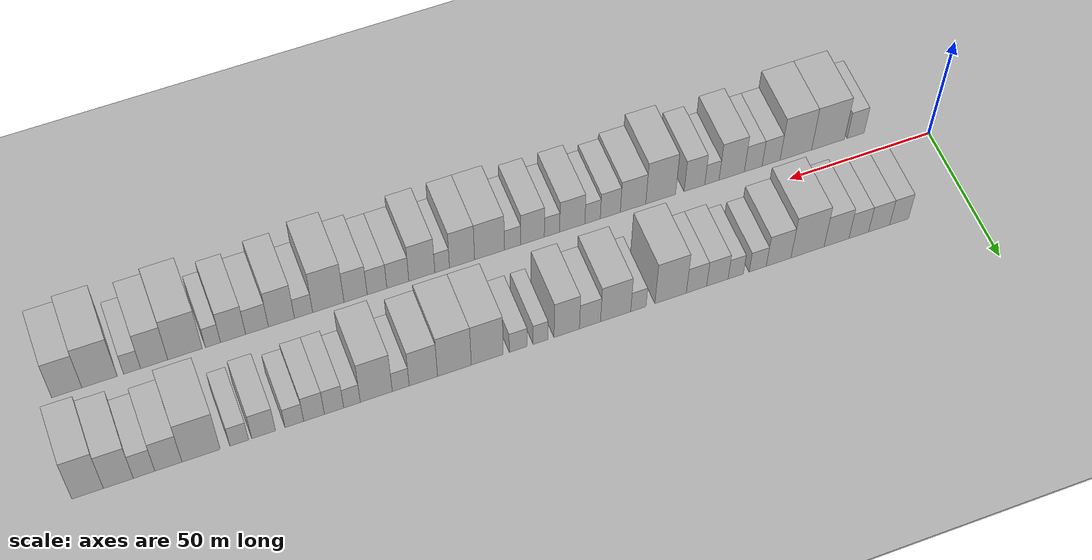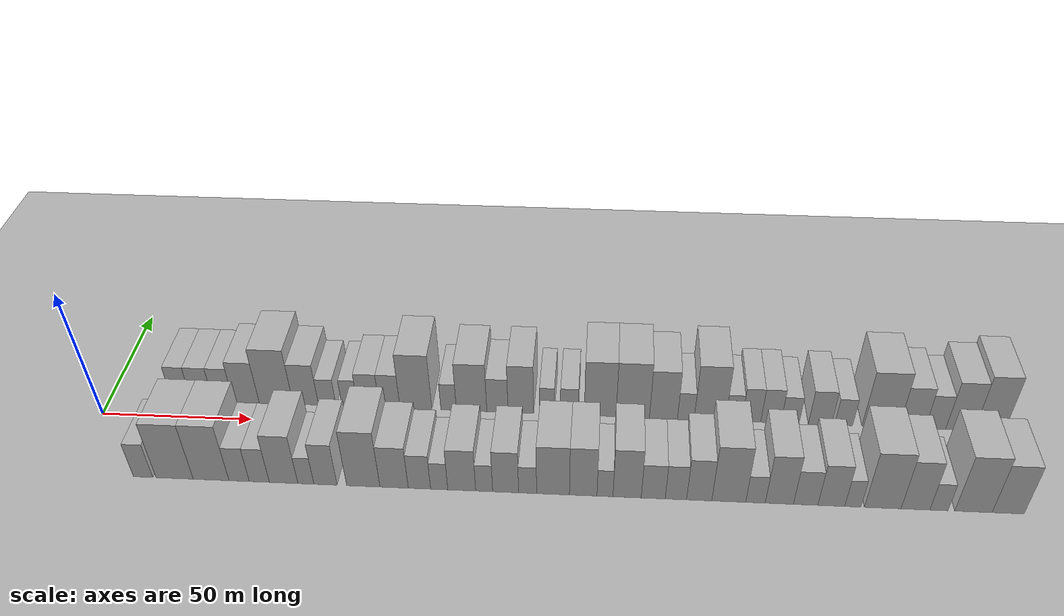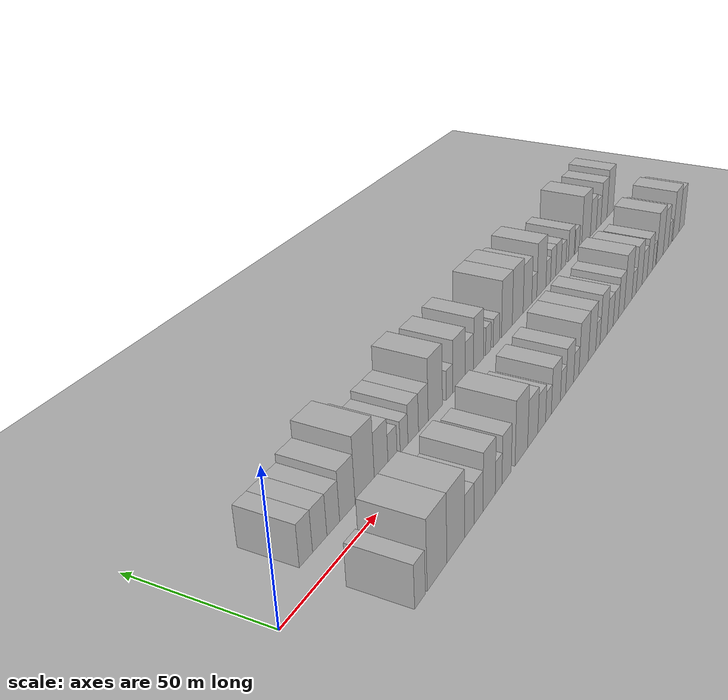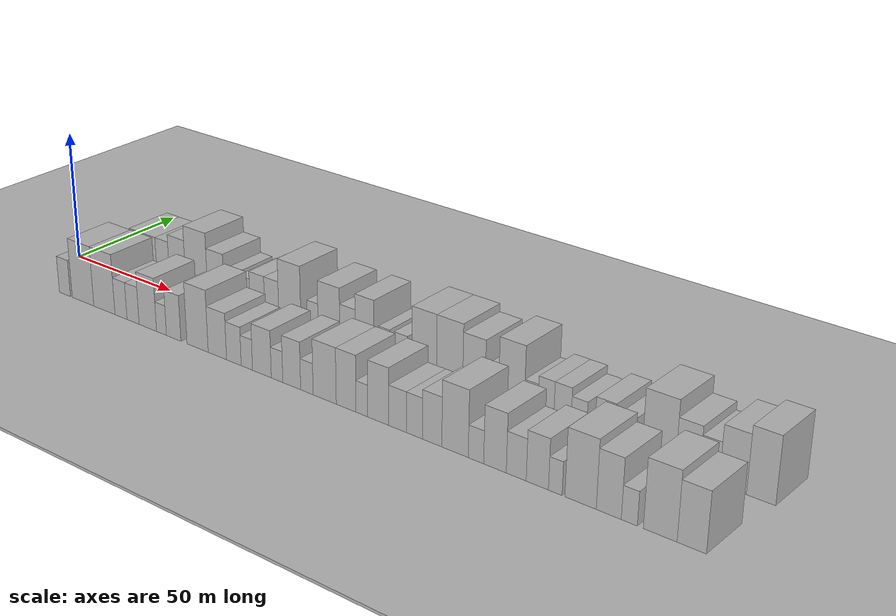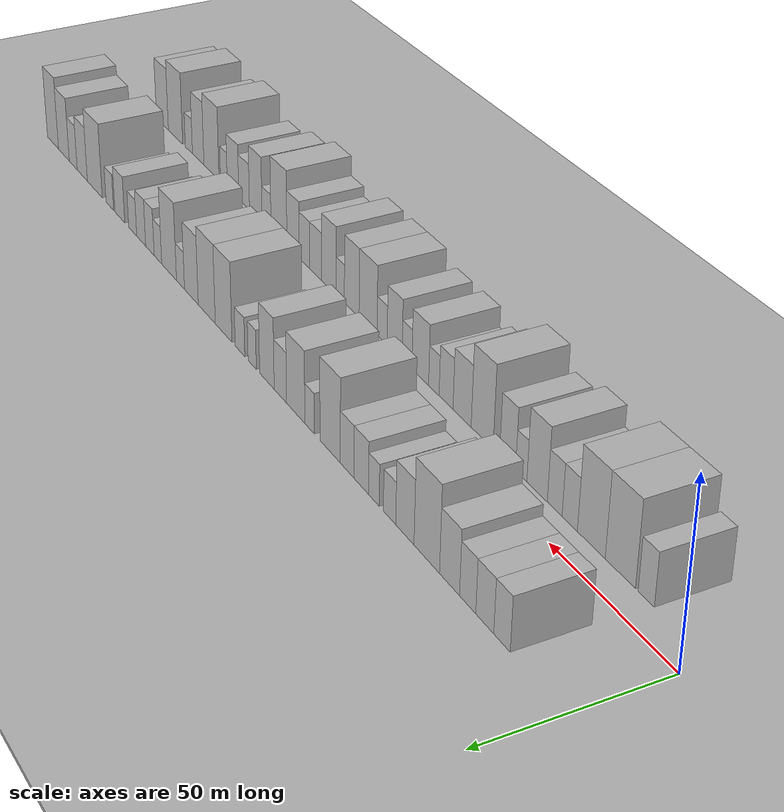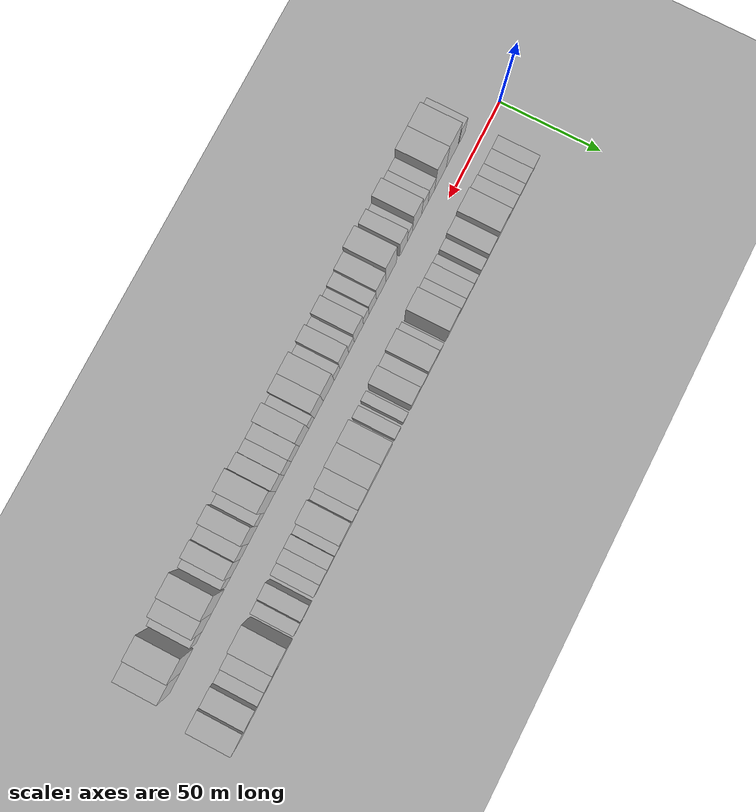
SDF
<?xml version="1.0" encoding="utf-8"?>

<sdf version="1.6">

   <world name="default">

      <gui fullscreen="0">

         <camera name="user_camera">

            <pose>-15 0 4.57585 0 0 0</pose>

            <view_controller>orbit</view_controller>

         </camera>

      </gui>

      <scene>

         <sky>

           <clouds>

             <speed>12</speed>

           </clouds>

         </sky>

         <ambient>0.4 0.4 0.4 1</ambient>

         <background>0.7 0.7 0.7 1</background>

         <shadows>1</shadows>

      </scene>

      <gravity>0 0 -9.8066</gravity>

      <magnetic_field>6e-06 2.3e-05 -4.2e-05</magnetic_field>

      <physics default="0" name="default_physics" type="ode">

         <ode>

            <solver>

               <type>quick</type>

               <iters>10</iters>

               <sor>1.0</sor>

               <use_dynamic_moi_rescaling>0</use_dynamic_moi_rescaling>

            </solver>

            <constraints>

               <cfm>0</cfm>

               <erp>0.2</erp>

               <contact_max_correcting_vel>100</contact_max_correcting_vel>

               <contact_surface_layer>0.001</contact_surface_layer>

            </constraints>

         </ode>

         <max_step_size>0.004</max_step_size>

         <real_time_factor>1</real_time_factor>

         <real_time_update_rate>250</real_time_update_rate>

      </physics>

      <light name="sun" type="directional">

         <cast_shadows>1</cast_shadows>

         <pose>0 0 10 0 0 0</pose>

         <diffuse>0.8 0.8 0.8 1</diffuse>

         <specular>0.2 0.2 0.2 1</specular>

         <attenuation>

            <range>1000</range>

            <constant>0.9</constant>

            <linear>0.01</linear>

            <quadratic>0.001</quadratic>

         </attenuation>

         <direction>-0.5 0.1 -0.9</direction>

      </light>

      <include>

         <name>ground_plane_1</name>

         <uri>model://HANNAS_ground_plane</uri>

         <pose>0 0 0  0 0 0</pose>

      </include>

      <include>

         <name>ground_plane_2</name>

         <uri>model://HANNAS_ground_plane</uri>

         <pose>100 0 0  0 0 0</pose>

      </include>

      <model name="building_1">

         <static>1</static>

         <pose frame="">24.3293 17.5000 0 0.000000 0.000000 1.570796</pose>

         <link name="link">

            <pose frame="">0 0 7.50 0 0 0</pose>

            <collision name="collision">

               <geometry>

                  <box>

                     <size>20.0000 6.6587 15.0000</size>

                  </box>

               </geometry>

               <max_contacts>10</max_contacts>

               <surface>

                  <contact>

                     <ode/>

                  </contact>

                  <bounce/>

                  <friction>

                     <torsional>

                        <ode/>

                     </torsional>

                     <ode/>

                  </friction>

               </surface>

            </collision>

            <visual name="visual">

               <cast_shadows>0</cast_shadows>

               <geometry>

                  <box>

                     <size>20.0000 6.6587 15.0000</size>

                  </box>

               </geometry>

               <material>

                  <script>

                     <uri>model://HANNAS_wall/materials/scripts</uri>

                     <uri>model://HANNAS_wall/materials/textures</uri>

                     <name>vrc/HANNAS_wall</name>

                  </script>

               </material>

            </visual>

            <self_collide>0</self_collide>

            <enable_wind>0</enable_wind>

            <kinematic>0</kinematic>

         </link>

      </model>

      <model name="building_2">

         <static>1</static>

         <pose frame="">31.3864 17.5000 0 0.000000 0.000000 1.570796</pose>

         <link name="link">

            <pose frame="">0 0 7.50 0 0 0</pose>

            <collision name="collision">

               <geometry>

                  <box>

                     <size>20.0000 7.4555 15.0000</size>

                  </box>

               </geometry>

               <max_contacts>10</max_contacts>

               <surface>

                  <contact>

                     <ode/>

                  </contact>

                  <bounce/>

                  <friction>

                     <torsional>

                        <ode/>

                     </torsional>

                     <ode/>

                  </friction>

               </surface>

            </collision>

            <visual name="visual">

               <cast_shadows>0</cast_shadows>

               <geometry>

                  <box>

                     <size>20.0000 7.4555 15.0000</size>

                  </box>

               </geometry>

               <material>

                  <script>

                     <uri>model://HANNAS_wall/materials/scripts</uri>

                     <uri>model://HANNAS_wall/materials/textures</uri>

                     <name>vrc/HANNAS_wall</name>

                  </script>

               </material>

            </visual>

            <self_collide>0</self_collide>

            <enable_wind>0</enable_wind>

            <kinematic>0</kinematic>

         </link>

      </model>

      <model name="building_3">

         <static>1</static>

         <pose frame="">38.5593 17.5000 0 0.000000 0.000000 1.570796</pose>

         <link name="link">

            <pose frame="">0 0 7.50 0 0 0</pose>

            <collision name="collision">

               <geometry>

                  <box>

                     <size>20.0000 6.8902 15.0000</size>

                  </box>

               </geometry>

               <max_contacts>10</max_contacts>

               <surface>

                  <contact>

                     <ode/>

                  </contact>

                  <bounce/>

                  <friction>

                     <torsional>

                        <ode/>

                     </torsional>

                     <ode/>

                  </friction>

               </surface>

            </collision>

            <visual name="visual">

               <cast_shadows>0</cast_shadows>

               <geometry>

                  <box>

                     <size>20.0000 6.8902 15.0000</size>

                  </box>

               </geometry>

               <material>

                  <script>

                     <uri>model://HANNAS_wall/materials/scripts</uri>

                     <uri>model://HANNAS_wall/materials/textures</uri>

                     <name>vrc/HANNAS_wall</name>

                  </script>

               </material>

            </visual>

            <self_collide>0</self_collide>

            <enable_wind>0</enable_wind>

            <kinematic>0</kinematic>

         </link>

      </model>

      <model name="building_4">

         <static>1</static>

         <pose frame="">46.3622 17.5000 0 0.000000 0.000000 1.570796</pose>

         <link name="link">

            <pose frame="">0 0 9.00 0 0 0</pose>

            <collision name="collision">

               <geometry>

                  <box>

                     <size>20.0000 8.7157 18.0000</size>

                  </box>

               </geometry>

               <max_contacts>10</max_contacts>

               <surface>

                  <contact>

                     <ode/>

                  </contact>

                  <bounce/>

                  <friction>

                     <torsional>

                        <ode/>

                     </torsional>

                     <ode/>

                  </friction>

               </surface>

            </collision>

            <visual name="visual">

               <cast_shadows>0</cast_shadows>

               <geometry>

                  <box>

                     <size>20.0000 8.7157 18.0000</size>

                  </box>

               </geometry>

               <material>

                  <script>

                     <uri>model://HANNAS_wall/materials/scripts</uri>

                     <uri>model://HANNAS_wall/materials/textures</uri>

                     <name>vrc/HANNAS_wall</name>

                  </script>

               </material>

            </visual>

            <self_collide>0</self_collide>

            <enable_wind>0</enable_wind>

            <kinematic>0</kinematic>

         </link>

      </model>

      <model name="building_5">

         <static>1</static>

         <pose frame="">56.4723 17.5000 0 0.000000 0.000000 1.570796</pose>

         <link name="link">

            <pose frame="">0 0 12.00 0 0 0</pose>

            <collision name="collision">

               <geometry>

                  <box>

                     <size>20.0000 11.5045 24.0000</size>

                  </box>

               </geometry>

               <max_contacts>10</max_contacts>

               <surface>

                  <contact>

                     <ode/>

                  </contact>

                  <bounce/>

                  <friction>

                     <torsional>

                        <ode/>

                     </torsional>

                     <ode/>

                  </friction>

               </surface>

            </collision>

            <visual name="visual">

               <cast_shadows>0</cast_shadows>

               <geometry>

                  <box>

                     <size>20.0000 11.5045 24.0000</size>

                  </box>

               </geometry>

               <material>

                  <script>

                     <uri>model://HANNAS_wall/materials/scripts</uri>

                     <uri>model://HANNAS_wall/materials/textures</uri>

                     <name>vrc/HANNAS_wall</name>

                  </script>

               </material>

            </visual>

            <self_collide>0</self_collide>

            <enable_wind>0</enable_wind>

            <kinematic>0</kinematic>

         </link>

      </model>

      <model name="building_6">

         <static>1</static>

         <pose frame="">66.5000 17.5000 0 0.000000 0.000000 1.570796</pose>

         <link name="link">

            <pose frame="">0 0 9.00 0 0 0</pose>

            <collision name="collision">

               <geometry>

                  <box>

                     <size>20.0000 8.5510 18.0000</size>

                  </box>

               </geometry>

               <max_contacts>10</max_contacts>

               <surface>

                  <contact>

                     <ode/>

                  </contact>

                  <bounce/>

                  <friction>

                     <torsional>

                        <ode/>

                     </torsional>

                     <ode/>

                  </friction>

               </surface>

            </collision>

            <visual name="visual">

               <cast_shadows>0</cast_shadows>

               <geometry>

                  <box>

                     <size>20.0000 8.5510 18.0000</size>

                  </box>

               </geometry>

               <material>

                  <script>

                     <uri>model://HANNAS_wall/materials/scripts</uri>

                     <uri>model://HANNAS_wall/materials/textures</uri>

                     <name>vrc/HANNAS_wall</name>

                  </script>

               </material>

            </visual>

            <self_collide>0</self_collide>

            <enable_wind>0</enable_wind>

            <kinematic>0</kinematic>

         </link>

      </model>

      <model name="building_7">

         <static>1</static>

         <pose frame="">73.7174 17.5000 0 0.000000 0.000000 1.570796</pose>

         <link name="link">

            <pose frame="">0 0 6.00 0 0 0</pose>

            <collision name="collision">

               <geometry>

                  <box>

                     <size>20.0000 5.8837 12.0000</size>

                  </box>

               </geometry>

               <max_contacts>10</max_contacts>

               <surface>

                  <contact>

                     <ode/>

                  </contact>

                  <bounce/>

                  <friction>

                     <torsional>

                        <ode/>

                     </torsional>

                     <ode/>

                  </friction>

               </surface>

            </collision>

            <visual name="visual">

               <cast_shadows>0</cast_shadows>

               <geometry>

                  <box>

                     <size>20.0000 5.8837 12.0000</size>

                  </box>

               </geometry>

               <material>

                  <script>

                     <uri>model://HANNAS_wall/materials/scripts</uri>

                     <uri>model://HANNAS_wall/materials/textures</uri>

                     <name>vrc/HANNAS_wall</name>

                  </script>

               </material>

            </visual>

            <self_collide>0</self_collide>

            <enable_wind>0</enable_wind>

            <kinematic>0</kinematic>

         </link>

      </model>

      <model name="building_8">

         <static>1</static>

         <pose frame="">81.2835 17.5000 0 0.000000 0.000000 1.570796</pose>

         <link name="link">

            <pose frame="">0 0 6.00 0 0 0</pose>

            <collision name="collision">

               <geometry>

                  <box>

                     <size>20.0000 5.2485 12.0000</size>

                  </box>

               </geometry>

               <max_contacts>10</max_contacts>

               <surface>

                  <contact>

                     <ode/>

                  </contact>

                  <bounce/>

                  <friction>

                     <torsional>

                        <ode/>

                     </torsional>

                     <ode/>

                  </friction>

               </surface>

            </collision>

            <visual name="visual">

               <cast_shadows>0</cast_shadows>

               <geometry>

                  <box>

                     <size>20.0000 5.2485 12.0000</size>

                  </box>

               </geometry>

               <material>

                  <script>

                     <uri>model://HANNAS_wall/materials/scripts</uri>

                     <uri>model://HANNAS_wall/materials/textures</uri>

                     <name>vrc/HANNAS_wall</name>

                  </script>

               </material>

            </visual>

            <self_collide>0</self_collide>

            <enable_wind>0</enable_wind>

            <kinematic>0</kinematic>

         </link>

      </model>

      <model name="building_9">

         <static>1</static>

         <pose frame="">87.5686 17.5000 0 0.000000 0.000000 1.570796</pose>

         <link name="link">

            <pose frame="">0 0 7.50 0 0 0</pose>

            <collision name="collision">

               <geometry>

                  <box>

                     <size>20.0000 7.3218 15.0000</size>

                  </box>

               </geometry>

               <max_contacts>10</max_contacts>

               <surface>

                  <contact>

                     <ode/>

                  </contact>

                  <bounce/>

                  <friction>

                     <torsional>

                        <ode/>

                     </torsional>

                     <ode/>

                  </friction>

               </surface>

            </collision>

            <visual name="visual">

               <cast_shadows>0</cast_shadows>

               <geometry>

                  <box>

                     <size>20.0000 7.3218 15.0000</size>

                  </box>

               </geometry>

               <material>

                  <script>

                     <uri>model://HANNAS_wall/materials/scripts</uri>

                     <uri>model://HANNAS_wall/materials/textures</uri>

                     <name>vrc/HANNAS_wall</name>

                  </script>

               </material>

            </visual>

            <self_collide>0</self_collide>

            <enable_wind>0</enable_wind>

            <kinematic>0</kinematic>

         </link>

      </model>

      <model name="building_10">

         <static>1</static>

         <pose frame="">94.6913 17.5000 0 0.000000 0.000000 1.570796</pose>

         <link name="link">

            <pose frame="">0 0 7.50 0 0 0</pose>

            <collision name="collision">

               <geometry>

                  <box>

                     <size>20.0000 6.9235 15.0000</size>

                  </box>

               </geometry>

               <max_contacts>10</max_contacts>

               <surface>

                  <contact>

                     <ode/>

                  </contact>

                  <bounce/>

                  <friction>

                     <torsional>

                        <ode/>

                     </torsional>

                     <ode/>

                  </friction>

               </surface>

            </collision>

            <visual name="visual">

               <cast_shadows>0</cast_shadows>

               <geometry>

                  <box>

                     <size>20.0000 6.9235 15.0000</size>

                  </box>

               </geometry>

               <material>

                  <script>

                     <uri>model://HANNAS_wall/materials/scripts</uri>

                     <uri>model://HANNAS_wall/materials/textures</uri>

                     <name>vrc/HANNAS_wall</name>

                  </script>

               </material>

            </visual>

            <self_collide>0</self_collide>

            <enable_wind>0</enable_wind>

            <kinematic>0</kinematic>

         </link>

      </model>

      <model name="building_11">

         <static>1</static>

         <pose frame="">103.4852 17.5000 0 0.000000 0.000000 1.570796</pose>

         <link name="link">

            <pose frame="">0 0 12.00 0 0 0</pose>

            <collision name="collision">

               <geometry>

                  <box>

                     <size>20.0000 10.6644 24.0000</size>

                  </box>

               </geometry>

               <max_contacts>10</max_contacts>

               <surface>

                  <contact>

                     <ode/>

                  </contact>

                  <bounce/>

                  <friction>

                     <torsional>

                        <ode/>

                     </torsional>

                     <ode/>

                  </friction>

               </surface>

            </collision>

            <visual name="visual">

               <cast_shadows>0</cast_shadows>

               <geometry>

                  <box>

                     <size>20.0000 10.6644 24.0000</size>

                  </box>

               </geometry>

               <material>

                  <script>

                     <uri>model://HANNAS_wall/materials/scripts</uri>

                     <uri>model://HANNAS_wall/materials/textures</uri>

                     <name>vrc/HANNAS_wall</name>

                  </script>

               </material>

            </visual>

            <self_collide>0</self_collide>

            <enable_wind>0</enable_wind>

            <kinematic>0</kinematic>

         </link>

      </model>

      <model name="building_12">

         <static>1</static>

         <pose frame="">114.4038 17.5000 0 0.000000 0.000000 1.570796</pose>

         <link name="link">

            <pose frame="">0 0 6.00 0 0 0</pose>

            <collision name="collision">

               <geometry>

                  <box>

                     <size>20.0000 5.1728 12.0000</size>

                  </box>

               </geometry>

               <max_contacts>10</max_contacts>

               <surface>

                  <contact>

                     <ode/>

                  </contact>

                  <bounce/>

                  <friction>

                     <torsional>

                        <ode/>

                     </torsional>

                     <ode/>

                  </friction>

               </surface>

            </collision>

            <visual name="visual">

               <cast_shadows>0</cast_shadows>

               <geometry>

                  <box>

                     <size>20.0000 5.1728 12.0000</size>

                  </box>

               </geometry>

               <material>

                  <script>

                     <uri>model://HANNAS_wall/materials/scripts</uri>

                     <uri>model://HANNAS_wall/materials/textures</uri>

                     <name>vrc/HANNAS_wall</name>

                  </script>

               </material>

            </visual>

            <self_collide>0</self_collide>

            <enable_wind>0</enable_wind>

            <kinematic>0</kinematic>

         </link>

      </model>

      <model name="building_13">

         <static>1</static>

         <pose frame="">122.0544 17.5000 0 0.000000 0.000000 1.570796</pose>

         <link name="link">

            <pose frame="">0 0 10.50 0 0 0</pose>

            <collision name="collision">

               <geometry>

                  <box>

                     <size>20.0000 10.1282 21.0000</size>

                  </box>

               </geometry>

               <max_contacts>10</max_contacts>

               <surface>

                  <contact>

                     <ode/>

                  </contact>

                  <bounce/>

                  <friction>

                     <torsional>

                        <ode/>

                     </torsional>

                     <ode/>

                  </friction>

               </surface>

            </collision>

            <visual name="visual">

               <cast_shadows>0</cast_shadows>

               <geometry>

                  <box>

                     <size>20.0000 10.1282 21.0000</size>

                  </box>

               </geometry>

               <material>

                  <script>

                     <uri>model://HANNAS_wall/materials/scripts</uri>

                     <uri>model://HANNAS_wall/materials/textures</uri>

                     <name>vrc/HANNAS_wall</name>

                  </script>

               </material>

            </visual>

            <self_collide>0</self_collide>

            <enable_wind>0</enable_wind>

            <kinematic>0</kinematic>

         </link>

      </model>

      <model name="building_14">

         <static>1</static>

         <pose frame="">130.6511 17.5000 0 0.000000 0.000000 1.570796</pose>

         <link name="link">

            <pose frame="">0 0 7.50 0 0 0</pose>

            <collision name="collision">

               <geometry>

                  <box>

                     <size>20.0000 7.0652 15.0000</size>

                  </box>

               </geometry>

               <max_contacts>10</max_contacts>

               <surface>

                  <contact>

                     <ode/>

                  </contact>

                  <bounce/>

                  <friction>

                     <torsional>

                        <ode/>

                     </torsional>

                     <ode/>

                  </friction>

               </surface>

            </collision>

            <visual name="visual">

               <cast_shadows>0</cast_shadows>

               <geometry>

                  <box>

                     <size>20.0000 7.0652 15.0000</size>

                  </box>

               </geometry>

               <material>

                  <script>

                     <uri>model://HANNAS_wall/materials/scripts</uri>

                     <uri>model://HANNAS_wall/materials/textures</uri>

                     <name>vrc/HANNAS_wall</name>

                  </script>

               </material>

            </visual>

            <self_collide>0</self_collide>

            <enable_wind>0</enable_wind>

            <kinematic>0</kinematic>

         </link>

      </model>

      <model name="building_15">

         <static>1</static>

         <pose frame="">138.4211 17.5000 0 0.000000 0.000000 1.570796</pose>

         <link name="link">

            <pose frame="">0 0 10.50 0 0 0</pose>

            <collision name="collision">

               <geometry>

                  <box>

                     <size>20.0000 8.4748 21.0000</size>

                  </box>

               </geometry>

               <max_contacts>10</max_contacts>

               <surface>

                  <contact>

                     <ode/>

                  </contact>

                  <bounce/>

                  <friction>

                     <torsional>

                        <ode/>

                     </torsional>

                     <ode/>

                  </friction>

               </surface>

            </collision>

            <visual name="visual">

               <cast_shadows>0</cast_shadows>

               <geometry>

                  <box>

                     <size>20.0000 8.4748 21.0000</size>

                  </box>

               </geometry>

               <material>

                  <script>

                     <uri>model://HANNAS_wall/materials/scripts</uri>

                     <uri>model://HANNAS_wall/materials/textures</uri>

                     <name>vrc/HANNAS_wall</name>

                  </script>

               </material>

            </visual>

            <self_collide>0</self_collide>

            <enable_wind>0</enable_wind>

            <kinematic>0</kinematic>

         </link>

      </model>

      <model name="building_16">

         <static>1</static>

         <pose frame="">147.1039 17.5000 0 0.000000 0.000000 1.570796</pose>

         <link name="link">

            <pose frame="">0 0 6.00 0 0 0</pose>

            <collision name="collision">

               <geometry>

                  <box>

                     <size>20.0000 4.8908 12.0000</size>

                  </box>

               </geometry>

               <max_contacts>10</max_contacts>

               <surface>

                  <contact>

                     <ode/>

                  </contact>

                  <bounce/>

                  <friction>

                     <torsional>

                        <ode/>

                     </torsional>

                     <ode/>

                  </friction>

               </surface>

            </collision>

            <visual name="visual">

               <cast_shadows>0</cast_shadows>

               <geometry>

                  <box>

                     <size>20.0000 4.8908 12.0000</size>

                  </box>

               </geometry>

               <material>

                  <script>

                     <uri>model://HANNAS_wall/materials/scripts</uri>

                     <uri>model://HANNAS_wall/materials/textures</uri>

                     <name>vrc/HANNAS_wall</name>

                  </script>

               </material>

            </visual>

            <self_collide>0</self_collide>

            <enable_wind>0</enable_wind>

            <kinematic>0</kinematic>

         </link>

      </model>

      <model name="building_17">

         <static>1</static>

         <pose frame="">154.4874 17.5000 0 0.000000 0.000000 1.570796</pose>

         <link name="link">

            <pose frame="">0 0 6.00 0 0 0</pose>

            <collision name="collision">

               <geometry>

                  <box>

                     <size>20.0000 5.8762 12.0000</size>

                  </box>

               </geometry>

               <max_contacts>10</max_contacts>

               <surface>

                  <contact>

                     <ode/>

                  </contact>

                  <bounce/>

                  <friction>

                     <torsional>

                        <ode/>

                     </torsional>

                     <ode/>

                  </friction>

               </surface>

            </collision>

            <visual name="visual">

               <cast_shadows>0</cast_shadows>

               <geometry>

                  <box>

                     <size>20.0000 5.8762 12.0000</size>

                  </box>

               </geometry>

               <material>

                  <script>

                     <uri>model://HANNAS_wall/materials/scripts</uri>

                     <uri>model://HANNAS_wall/materials/textures</uri>

                     <name>vrc/HANNAS_wall</name>

                  </script>

               </material>

            </visual>

            <self_collide>0</self_collide>

            <enable_wind>0</enable_wind>

            <kinematic>0</kinematic>

         </link>

      </model>

      <model name="building_18">

         <static>1</static>

         <pose frame="">164.6580 17.5000 0 0.000000 0.000000 1.570796</pose>

         <link name="link">

            <pose frame="">0 0 12.00 0 0 0</pose>

            <collision name="collision">

               <geometry>

                  <box>

                     <size>20.0000 10.4650 24.0000</size>

                  </box>

               </geometry>

               <max_contacts>10</max_contacts>

               <surface>

                  <contact>

                     <ode/>

                  </contact>

                  <bounce/>

                  <friction>

                     <torsional>

                        <ode/>

                     </torsional>

                     <ode/>

                  </friction>

               </surface>

            </collision>

            <visual name="visual">

               <cast_shadows>0</cast_shadows>

               <geometry>

                  <box>

                     <size>20.0000 10.4650 24.0000</size>

                  </box>

               </geometry>

               <material>

                  <script>

                     <uri>model://HANNAS_wall/materials/scripts</uri>

                     <uri>model://HANNAS_wall/materials/textures</uri>

                     <name>vrc/HANNAS_wall</name>

                  </script>

               </material>

            </visual>

            <self_collide>0</self_collide>

            <enable_wind>0</enable_wind>

            <kinematic>0</kinematic>

         </link>

      </model>

      <model name="building_19">

         <static>1</static>

         <pose frame="">175.4049 17.5000 0 0.000000 0.000000 1.570796</pose>

         <link name="link">

            <pose frame="">0 0 12.00 0 0 0</pose>

            <collision name="collision">

               <geometry>

                  <box>

                     <size>20.0000 11.0287 24.0000</size>

                  </box>

               </geometry>

               <max_contacts>10</max_contacts>

               <surface>

                  <contact>

                     <ode/>

                  </contact>

                  <bounce/>

                  <friction>

                     <torsional>

                        <ode/>

                     </torsional>

                     <ode/>

                  </friction>

               </surface>

            </collision>

            <visual name="visual">

               <cast_shadows>0</cast_shadows>

               <geometry>

                  <box>

                     <size>20.0000 11.0287 24.0000</size>

                  </box>

               </geometry>

               <material>

                  <script>

                     <uri>model://HANNAS_wall/materials/scripts</uri>

                     <uri>model://HANNAS_wall/materials/textures</uri>

                     <name>vrc/HANNAS_wall</name>

                  </script>

               </material>

            </visual>

            <self_collide>0</self_collide>

            <enable_wind>0</enable_wind>

            <kinematic>0</kinematic>

         </link>

      </model>

      <model name="building_20">

         <static>1</static>

         <pose frame="">185.5153 17.5000 0 0.000000 0.000000 1.570796</pose>

         <link name="link">

            <pose frame="">0 0 10.50 0 0 0</pose>

            <collision name="collision">

               <geometry>

                  <box>

                     <size>20.0000 9.1920 21.0000</size>

                  </box>

               </geometry>

               <max_contacts>10</max_contacts>

               <surface>

                  <contact>

                     <ode/>

                  </contact>

                  <bounce/>

                  <friction>

                     <torsional>

                        <ode/>

                     </torsional>

                     <ode/>

                  </friction>

               </surface>

            </collision>

            <visual name="visual">

               <cast_shadows>0</cast_shadows>

               <geometry>

                  <box>

                     <size>20.0000 9.1920 21.0000</size>

                  </box>

               </geometry>

               <material>

                  <script>

                     <uri>model://HANNAS_wall/materials/scripts</uri>

                     <uri>model://HANNAS_wall/materials/textures</uri>

                     <name>vrc/HANNAS_wall</name>

                  </script>

               </material>

            </visual>

            <self_collide>0</self_collide>

            <enable_wind>0</enable_wind>

            <kinematic>0</kinematic>

         </link>

      </model>

      <model name="building_21">

         <static>1</static>

         <pose frame="">192.8316 17.5000 0 0.000000 0.000000 1.570796</pose>

         <link name="link">

            <pose frame="">0 0 6.00 0 0 0</pose>

            <collision name="collision">

               <geometry>

                  <box>

                     <size>20.0000 5.4407 12.0000</size>

                  </box>

               </geometry>

               <max_contacts>10</max_contacts>

               <surface>

                  <contact>

                     <ode/>

                  </contact>

                  <bounce/>

                  <friction>

                     <torsional>

                        <ode/>

                     </torsional>

                     <ode/>

                  </friction>

               </surface>

            </collision>

            <visual name="visual">

               <cast_shadows>0</cast_shadows>

               <geometry>

                  <box>

                     <size>20.0000 5.4407 12.0000</size>

                  </box>

               </geometry>

               <material>

                  <script>

                     <uri>model://HANNAS_wall/materials/scripts</uri>

                     <uri>model://HANNAS_wall/materials/textures</uri>

                     <name>vrc/HANNAS_wall</name>

                  </script>

               </material>

            </visual>

            <self_collide>0</self_collide>

            <enable_wind>0</enable_wind>

            <kinematic>0</kinematic>

         </link>

      </model>

      <model name="building_22">

         <static>1</static>

         <pose frame="">200.6947 17.5000 0 0.000000 0.000000 1.570796</pose>

         <link name="link">

            <pose frame="">0 0 12.00 0 0 0</pose>

            <collision name="collision">

               <geometry>

                  <box>

                     <size>20.0000 10.2853 24.0000</size>

                  </box>

               </geometry>

               <max_contacts>10</max_contacts>

               <surface>

                  <contact>

                     <ode/>

                  </contact>

                  <bounce/>

                  <friction>

                     <torsional>

                        <ode/>

                     </torsional>

                     <ode/>

                  </friction>

               </surface>

            </collision>

            <visual name="visual">

               <cast_shadows>0</cast_shadows>

               <geometry>

                  <box>

                     <size>20.0000 10.2853 24.0000</size>

                  </box>

               </geometry>

               <material>

                  <script>

                     <uri>model://HANNAS_wall/materials/scripts</uri>

                     <uri>model://HANNAS_wall/materials/textures</uri>

                     <name>vrc/HANNAS_wall</name>

                  </script>

               </material>

            </visual>

            <self_collide>0</self_collide>

            <enable_wind>0</enable_wind>

            <kinematic>0</kinematic>

         </link>

      </model>

      <model name="building_23">

         <static>1</static>

         <pose frame="">208.5004 17.5000 0 0.000000 0.000000 1.570796</pose>

         <link name="link">

            <pose frame="">0 0 6.00 0 0 0</pose>

            <collision name="collision">

               <geometry>

                  <box>

                     <size>20.0000 5.3262 12.0000</size>

                  </box>

               </geometry>

               <max_contacts>10</max_contacts>

               <surface>

                  <contact>

                     <ode/>

                  </contact>

                  <bounce/>

                  <friction>

                     <torsional>

                        <ode/>

                     </torsional>

                     <ode/>

                  </friction>

               </surface>

            </collision>

            <visual name="visual">

               <cast_shadows>0</cast_shadows>

               <geometry>

                  <box>

                     <size>20.0000 5.3262 12.0000</size>

                  </box>

               </geometry>

               <material>

                  <script>

                     <uri>model://HANNAS_wall/materials/scripts</uri>

                     <uri>model://HANNAS_wall/materials/textures</uri>

                     <name>vrc/HANNAS_wall</name>

                  </script>

               </material>

            </visual>

            <self_collide>0</self_collide>

            <enable_wind>0</enable_wind>

            <kinematic>0</kinematic>

         </link>

      </model>

      <model name="building_24">

         <static>1</static>

         <pose frame="">214.2465 17.5000 0 0.000000 0.000000 1.570796</pose>

         <link name="link">

            <pose frame="">0 0 7.50 0 0 0</pose>

            <collision name="collision">

               <geometry>

                  <box>

                     <size>20.0000 6.1659 15.0000</size>

                  </box>

               </geometry>

               <max_contacts>10</max_contacts>

               <surface>

                  <contact>

                     <ode/>

                  </contact>

                  <bounce/>

                  <friction>

                     <torsional>

                        <ode/>

                     </torsional>

                     <ode/>

                  </friction>

               </surface>

            </collision>

            <visual name="visual">

               <cast_shadows>0</cast_shadows>

               <geometry>

                  <box>

                     <size>20.0000 6.1659 15.0000</size>

                  </box>

               </geometry>

               <material>

                  <script>

                     <uri>model://HANNAS_wall/materials/scripts</uri>

                     <uri>model://HANNAS_wall/materials/textures</uri>

                     <name>vrc/HANNAS_wall</name>

                  </script>

               </material>

            </visual>

            <self_collide>0</self_collide>

            <enable_wind>0</enable_wind>

            <kinematic>0</kinematic>

         </link>

      </model>

      <model name="building_25">

         <static>1</static>

         <pose frame="">220.6165 17.5000 0 0.000000 0.000000 1.570796</pose>

         <link name="link">

            <pose frame="">0 0 7.50 0 0 0</pose>

            <collision name="collision">

               <geometry>

                  <box>

                     <size>20.0000 6.5742 15.0000</size>

                  </box>

               </geometry>

               <max_contacts>10</max_contacts>

               <surface>

                  <contact>

                     <ode/>

                  </contact>

                  <bounce/>

                  <friction>

                     <torsional>

                        <ode/>

                     </torsional>

                     <ode/>

                  </friction>

               </surface>

            </collision>

            <visual name="visual">

               <cast_shadows>0</cast_shadows>

               <geometry>

                  <box>

                     <size>20.0000 6.5742 15.0000</size>

                  </box>

               </geometry>

               <material>

                  <script>

                     <uri>model://HANNAS_wall/materials/scripts</uri>

                     <uri>model://HANNAS_wall/materials/textures</uri>

                     <name>vrc/HANNAS_wall</name>

                  </script>

               </material>

            </visual>

            <self_collide>0</self_collide>

            <enable_wind>0</enable_wind>

            <kinematic>0</kinematic>

         </link>

      </model>

      <model name="building_26">

         <static>1</static>

         <pose frame="">226.8721 17.5000 0 0.000000 0.000000 1.570796</pose>

         <link name="link">

            <pose frame="">0 0 6.00 0 0 0</pose>

            <collision name="collision">

               <geometry>

                  <box>

                     <size>20.0000 5.9371 12.0000</size>

                  </box>

               </geometry>

               <max_contacts>10</max_contacts>

               <surface>

                  <contact>

                     <ode/>

                  </contact>

                  <bounce/>

                  <friction>

                     <torsional>

                        <ode/>

                     </torsional>

                     <ode/>

                  </friction>

               </surface>

            </collision>

            <visual name="visual">

               <cast_shadows>0</cast_shadows>

               <geometry>

                  <box>

                     <size>20.0000 5.9371 12.0000</size>

                  </box>

               </geometry>

               <material>

                  <script>

                     <uri>model://HANNAS_wall/materials/scripts</uri>

                     <uri>model://HANNAS_wall/materials/textures</uri>

                     <name>vrc/HANNAS_wall</name>

                  </script>

               </material>

            </visual>

            <self_collide>0</self_collide>

            <enable_wind>0</enable_wind>

            <kinematic>0</kinematic>

         </link>

      </model>

      <model name="building_27">

         <static>1</static>

         <pose frame="">236.5884 17.5000 0 0.000000 0.000000 1.570796</pose>

         <link name="link">

            <pose frame="">0 0 7.50 0 0 0</pose>

            <collision name="collision">

               <geometry>

                  <box>

                     <size>20.0000 7.4955 15.0000</size>

                  </box>

               </geometry>

               <max_contacts>10</max_contacts>

               <surface>

                  <contact>

                     <ode/>

                  </contact>

                  <bounce/>

                  <friction>

                     <torsional>

                        <ode/>

                     </torsional>

                     <ode/>

                  </friction>

               </surface>

            </collision>

            <visual name="visual">

               <cast_shadows>0</cast_shadows>

               <geometry>

                  <box>

                     <size>20.0000 7.4955 15.0000</size>

                  </box>

               </geometry>

               <material>

                  <script>

                     <uri>model://HANNAS_wall/materials/scripts</uri>

                     <uri>model://HANNAS_wall/materials/textures</uri>

                     <name>vrc/HANNAS_wall</name>

                  </script>

               </material>

            </visual>

            <self_collide>0</self_collide>

            <enable_wind>0</enable_wind>

            <kinematic>0</kinematic>

         </link>

      </model>

      <model name="building_28">

         <static>1</static>

         <pose frame="">244.2812 17.5000 0 0.000000 0.000000 1.570796</pose>

         <link name="link">

            <pose frame="">0 0 6.00 0 0 0</pose>

            <collision name="collision">

               <geometry>

                  <box>

                     <size>20.0000 5.8900 12.0000</size>

                  </box>

               </geometry>

               <max_contacts>10</max_contacts>

               <surface>

                  <contact>

                     <ode/>

                  </contact>

                  <bounce/>

                  <friction>

                     <torsional>

                        <ode/>

                     </torsional>

                     <ode/>

                  </friction>

               </surface>

            </collision>

            <visual name="visual">

               <cast_shadows>0</cast_shadows>

               <geometry>

                  <box>

                     <size>20.0000 5.8900 12.0000</size>

                  </box>

               </geometry>

               <material>

                  <script>

                     <uri>model://HANNAS_wall/materials/scripts</uri>

                     <uri>model://HANNAS_wall/materials/textures</uri>

                     <name>vrc/HANNAS_wall</name>

                  </script>

               </material>

            </visual>

            <self_collide>0</self_collide>

            <enable_wind>0</enable_wind>

            <kinematic>0</kinematic>

         </link>

      </model>

      <model name="building_29">

         <static>1</static>

         <pose frame="">256.1907 17.5000 0 0.000000 0.000000 1.570796</pose>

         <link name="link">

            <pose frame="">0 0 12.00 0 0 0</pose>

            <collision name="collision">

               <geometry>

                  <box>

                     <size>20.0000 11.9292 24.0000</size>

                  </box>

               </geometry>

               <max_contacts>10</max_contacts>

               <surface>

                  <contact>

                     <ode/>

                  </contact>

                  <bounce/>

                  <friction>

                     <torsional>

                        <ode/>

                     </torsional>

                     <ode/>

                  </friction>

               </surface>

            </collision>

            <visual name="visual">

               <cast_shadows>0</cast_shadows>

               <geometry>

                  <box>

                     <size>20.0000 11.9292 24.0000</size>

                  </box>

               </geometry>

               <material>

                  <script>

                     <uri>model://HANNAS_wall/materials/scripts</uri>

                     <uri>model://HANNAS_wall/materials/textures</uri>

                     <name>vrc/HANNAS_wall</name>

                  </script>

               </material>

            </visual>

            <self_collide>0</self_collide>

            <enable_wind>0</enable_wind>

            <kinematic>0</kinematic>

         </link>

      </model>

      <model name="building_30">

         <static>1</static>

         <pose frame="">266.3586 17.5000 0 0.000000 0.000000 1.570796</pose>

         <link name="link">

            <pose frame="">0 0 9.00 0 0 0</pose>

            <collision name="collision">

               <geometry>

                  <box>

                     <size>20.0000 8.4065 18.0000</size>

                  </box>

               </geometry>

               <max_contacts>10</max_contacts>

               <surface>

                  <contact>

                     <ode/>

                  </contact>

                  <bounce/>

                  <friction>

                     <torsional>

                        <ode/>

                     </torsional>

                     <ode/>

                  </friction>

               </surface>

            </collision>

            <visual name="visual">

               <cast_shadows>0</cast_shadows>

               <geometry>

                  <box>

                     <size>20.0000 8.4065 18.0000</size>

                  </box>

               </geometry>

               <material>

                  <script>

                     <uri>model://HANNAS_wall/materials/scripts</uri>

                     <uri>model://HANNAS_wall/materials/textures</uri>

                     <name>vrc/HANNAS_wall</name>

                  </script>

               </material>

            </visual>

            <self_collide>0</self_collide>

            <enable_wind>0</enable_wind>

            <kinematic>0</kinematic>

         </link>

      </model>

      <model name="building_31">

         <static>1</static>

         <pose frame="">273.8908 17.5000 0 0.000000 0.000000 1.570796</pose>

         <link name="link">

            <pose frame="">0 0 7.50 0 0 0</pose>

            <collision name="collision">

               <geometry>

                  <box>

                     <size>20.0000 6.6580 15.0000</size>

                  </box>

               </geometry>

               <max_contacts>10</max_contacts>

               <surface>

                  <contact>

                     <ode/>

                  </contact>

                  <bounce/>

                  <friction>

                     <torsional>

                        <ode/>

                     </torsional>

                     <ode/>

                  </friction>

               </surface>

            </collision>

            <visual name="visual">

               <cast_shadows>0</cast_shadows>

               <geometry>

                  <box>

                     <size>20.0000 6.6580 15.0000</size>

                  </box>

               </geometry>

               <material>

                  <script>

                     <uri>model://HANNAS_wall/materials/scripts</uri>

                     <uri>model://HANNAS_wall/materials/textures</uri>

                     <name>vrc/HANNAS_wall</name>

                  </script>

               </material>

            </visual>

            <self_collide>0</self_collide>

            <enable_wind>0</enable_wind>

            <kinematic>0</kinematic>

         </link>

      </model>

      <model name="building_32">

         <static>1</static>

         <pose frame="">281.8167 17.5000 0 0.000000 0.000000 1.570796</pose>

         <link name="link">

            <pose frame="">0 0 10.50 0 0 0</pose>

            <collision name="collision">

               <geometry>

                  <box>

                     <size>20.0000 9.1938 21.0000</size>

                  </box>

               </geometry>

               <max_contacts>10</max_contacts>

               <surface>

                  <contact>

                     <ode/>

                  </contact>

                  <bounce/>

                  <friction>

                     <torsional>

                        <ode/>

                     </torsional>

                     <ode/>

                  </friction>

               </surface>

            </collision>

            <visual name="visual">

               <cast_shadows>0</cast_shadows>

               <geometry>

                  <box>

                     <size>20.0000 9.1938 21.0000</size>

                  </box>

               </geometry>

               <material>

                  <script>

                     <uri>model://HANNAS_wall/materials/scripts</uri>

                     <uri>model://HANNAS_wall/materials/textures</uri>

                     <name>vrc/HANNAS_wall</name>

                  </script>

               </material>

            </visual>

            <self_collide>0</self_collide>

            <enable_wind>0</enable_wind>

            <kinematic>0</kinematic>

         </link>

      </model>

      <model name="building_33">

         <static>1</static>

         <pose frame="">291.2391 17.5000 0 0.000000 0.000000 1.570796</pose>

         <link name="link">

            <pose frame="">0 0 12.00 0 0 0</pose>

            <collision name="collision">

               <geometry>

                  <box>

                     <size>20.0000 9.6509 24.0000</size>

                  </box>

               </geometry>

               <max_contacts>10</max_contacts>

               <surface>

                  <contact>

                     <ode/>

                  </contact>

                  <bounce/>

                  <friction>

                     <torsional>

                        <ode/>

                     </torsional>

                     <ode/>

                  </friction>

               </surface>

            </collision>

            <visual name="visual">

               <cast_shadows>0</cast_shadows>

               <geometry>

                  <box>

                     <size>20.0000 9.6509 24.0000</size>

                  </box>

               </geometry>

               <material>

                  <script>

                     <uri>model://HANNAS_wall/materials/scripts</uri>

                     <uri>model://HANNAS_wall/materials/textures</uri>

                     <name>vrc/HANNAS_wall</name>

                  </script>

               </material>

            </visual>

            <self_collide>0</self_collide>

            <enable_wind>0</enable_wind>

            <kinematic>0</kinematic>

         </link>

      </model>

      <model name="building_34">

         <static>1</static>

         <pose frame="">23.0649 -17.5000 0 0.000000 0.000000 1.570796</pose>

         <link name="link">

            <pose frame="">0 0 7.50 0 0 0</pose>

            <collision name="collision">

               <geometry>

                  <box>

                     <size>20.0000 6.1299 15.0000</size>

                  </box>

               </geometry>

               <max_contacts>10</max_contacts>

               <surface>

                  <contact>

                     <ode/>

                  </contact>

                  <bounce/>

                  <friction>

                     <torsional>

                        <ode/>

                     </torsional>

                     <ode/>

                  </friction>

               </surface>

            </collision>

            <visual name="visual">

               <cast_shadows>0</cast_shadows>

               <geometry>

                  <box>

                     <size>20.0000 6.1299 15.0000</size>

                  </box>

               </geometry>

               <material>

                  <script>

                     <uri>model://HANNAS_wall/materials/scripts</uri>

                     <uri>model://HANNAS_wall/materials/textures</uri>

                     <name>vrc/HANNAS_wall</name>

                  </script>

               </material>

            </visual>

            <self_collide>0</self_collide>

            <enable_wind>0</enable_wind>

            <kinematic>0</kinematic>

         </link>

      </model>

      <model name="building_35">

         <static>1</static>

         <pose frame="">33.0320 -17.5000 0 0.000000 0.000000 1.570796</pose>

         <link name="link">

            <pose frame="">0 0 12.00 0 0 0</pose>

            <collision name="collision">

               <geometry>

                  <box>

                     <size>20.0000 11.8043 24.0000</size>

                  </box>

               </geometry>

               <max_contacts>10</max_contacts>

               <surface>

                  <contact>

                     <ode/>

                  </contact>

                  <bounce/>

                  <friction>

                     <torsional>

                        <ode/>

                     </torsional>

                     <ode/>

                  </friction>

               </surface>

            </collision>

            <visual name="visual">

               <cast_shadows>0</cast_shadows>

               <geometry>

                  <box>

                     <size>20.0000 11.8043 24.0000</size>

                  </box>

               </geometry>

               <material>

                  <script>

                     <uri>model://HANNAS_wall/materials/scripts</uri>

                     <uri>model://HANNAS_wall/materials/textures</uri>

                     <name>vrc/HANNAS_wall</name>

                  </script>

               </material>

            </visual>

            <self_collide>0</self_collide>

            <enable_wind>0</enable_wind>

            <kinematic>0</kinematic>

         </link>

      </model>

      <model name="building_36">

         <static>1</static>

         <pose frame="">44.5746 -17.5000 0 0.000000 0.000000 1.570796</pose>

         <link name="link">

            <pose frame="">0 0 12.00 0 0 0</pose>

            <collision name="collision">

               <geometry>

                  <box>

                     <size>20.0000 11.2810 24.0000</size>

                  </box>

               </geometry>

               <max_contacts>10</max_contacts>

               <surface>

                  <contact>

                     <ode/>

                  </contact>

                  <bounce/>

                  <friction>

                     <torsional>

                        <ode/>

                     </torsional>

                     <ode/>

                  </friction>

               </surface>

            </collision>

            <visual name="visual">

               <cast_shadows>0</cast_shadows>

               <geometry>

                  <box>

                     <size>20.0000 11.2810 24.0000</size>

                  </box>

               </geometry>

               <material>

                  <script>

                     <uri>model://HANNAS_wall/materials/scripts</uri>

                     <uri>model://HANNAS_wall/materials/textures</uri>

                     <name>vrc/HANNAS_wall</name>

                  </script>

               </material>

            </visual>

            <self_collide>0</self_collide>

            <enable_wind>0</enable_wind>

            <kinematic>0</kinematic>

         </link>

      </model>

      <model name="building_37">

         <static>1</static>

         <pose frame="">53.4022 -17.5000 0 0.000000 0.000000 1.570796</pose>

         <link name="link">

            <pose frame="">0 0 7.50 0 0 0</pose>

            <collision name="collision">

               <geometry>

                  <box>

                     <size>20.0000 6.3742 15.0000</size>

                  </box>

               </geometry>

               <max_contacts>10</max_contacts>

               <surface>

                  <contact>

                     <ode/>

                  </contact>

                  <bounce/>

                  <friction>

                     <torsional>

                        <ode/>

                     </torsional>

                     <ode/>

                  </friction>

               </surface>

            </collision>

            <visual name="visual">

               <cast_shadows>0</cast_shadows>

               <geometry>

                  <box>

                     <size>20.0000 6.3742 15.0000</size>

                  </box>

               </geometry>

               <material>

                  <script>

                     <uri>model://HANNAS_wall/materials/scripts</uri>

                     <uri>model://HANNAS_wall/materials/textures</uri>

                     <name>vrc/HANNAS_wall</name>

                  </script>

               </material>

            </visual>

            <self_collide>0</self_collide>

            <enable_wind>0</enable_wind>

            <kinematic>0</kinematic>

         </link>

      </model>

      <model name="building_38">

         <static>1</static>

         <pose frame="">59.7423 -17.5000 0 0.000000 0.000000 1.570796</pose>

         <link name="link">

            <pose frame="">0 0 7.50 0 0 0</pose>

            <collision name="collision">

               <geometry>

                  <box>

                     <size>20.0000 6.3060 15.0000</size>

                  </box>

               </geometry>

               <max_contacts>10</max_contacts>

               <surface>

                  <contact>

                     <ode/>

                  </contact>

                  <bounce/>

                  <friction>

                     <torsional>

                        <ode/>

                     </torsional>

                     <ode/>

                  </friction>

               </surface>

            </collision>

            <visual name="visual">

               <cast_shadows>0</cast_shadows>

               <geometry>

                  <box>

                     <size>20.0000 6.3060 15.0000</size>

                  </box>

               </geometry>

               <material>

                  <script>

                     <uri>model://HANNAS_wall/materials/scripts</uri>

                     <uri>model://HANNAS_wall/materials/textures</uri>

                     <name>vrc/HANNAS_wall</name>

                  </script>

               </material>

            </visual>

            <self_collide>0</self_collide>

            <enable_wind>0</enable_wind>

            <kinematic>0</kinematic>

         </link>

      </model>

      <model name="building_39">

         <static>1</static>

         <pose frame="">67.3585 -17.5000 0 0.000000 0.000000 1.570796</pose>

         <link name="link">

            <pose frame="">0 0 10.50 0 0 0</pose>

            <collision name="collision">

               <geometry>

                  <box>

                     <size>20.0000 8.9265 21.0000</size>

                  </box>

               </geometry>

               <max_contacts>10</max_contacts>

               <surface>

                  <contact>

                     <ode/>

                  </contact>

                  <bounce/>

                  <friction>

                     <torsional>

                        <ode/>

                     </torsional>

                     <ode/>

                  </friction>

               </surface>

            </collision>

            <visual name="visual">

               <cast_shadows>0</cast_shadows>

               <geometry>

                  <box>

                     <size>20.0000 8.9265 21.0000</size>

                  </box>

               </geometry>

               <material>

                  <script>

                     <uri>model://HANNAS_wall/materials/scripts</uri>

                     <uri>model://HANNAS_wall/materials/textures</uri>

                     <name>vrc/HANNAS_wall</name>

                  </script>

               </material>

            </visual>

            <self_collide>0</self_collide>

            <enable_wind>0</enable_wind>

            <kinematic>0</kinematic>

         </link>

      </model>

      <model name="building_40">

         <static>1</static>

         <pose frame="">74.3347 -17.5000 0 0.000000 0.000000 1.570796</pose>

         <link name="link">

            <pose frame="">0 0 6.00 0 0 0</pose>

            <collision name="collision">

               <geometry>

                  <box>

                     <size>20.0000 5.0258 12.0000</size>

                  </box>

               </geometry>

               <max_contacts>10</max_contacts>

               <surface>

                  <contact>

                     <ode/>

                  </contact>

                  <bounce/>

                  <friction>

                     <torsional>

                        <ode/>

                     </torsional>

                     <ode/>

                  </friction>

               </surface>

            </collision>

            <visual name="visual">

               <cast_shadows>0</cast_shadows>

               <geometry>

                  <box>

                     <size>20.0000 5.0258 12.0000</size>

                  </box>

               </geometry>

               <material>

                  <script>

                     <uri>model://HANNAS_wall/materials/scripts</uri>

                     <uri>model://HANNAS_wall/materials/textures</uri>

                     <name>vrc/HANNAS_wall</name>

                  </script>

               </material>

            </visual>

            <self_collide>0</self_collide>

            <enable_wind>0</enable_wind>

            <kinematic>0</kinematic>

         </link>

      </model>

      <model name="building_41">

         <static>1</static>

         <pose frame="">80.4687 -17.5000 0 0.000000 0.000000 1.570796</pose>

         <link name="link">

            <pose frame="">0 0 9.00 0 0 0</pose>

            <collision name="collision">

               <geometry>

                  <box>

                     <size>20.0000 7.2424 18.0000</size>

                  </box>

               </geometry>

               <max_contacts>10</max_contacts>

               <surface>

                  <contact>

                     <ode/>

                  </contact>

                  <bounce/>

                  <friction>

                     <torsional>

                        <ode/>

                     </torsional>

                     <ode/>

                  </friction>

               </surface>

            </collision>

            <visual name="visual">

               <cast_shadows>0</cast_shadows>

               <geometry>

                  <box>

                     <size>20.0000 7.2424 18.0000</size>

                  </box>

               </geometry>

               <material>

                  <script>

                     <uri>model://HANNAS_wall/materials/scripts</uri>

                     <uri>model://HANNAS_wall/materials/textures</uri>

                     <name>vrc/HANNAS_wall</name>

                  </script>

               </material>

            </visual>

            <self_collide>0</self_collide>

            <enable_wind>0</enable_wind>

            <kinematic>0</kinematic>

         </link>

      </model>

      <model name="building_42">

         <static>1</static>

         <pose frame="">92.2791 -17.5000 0 0.000000 0.000000 1.570796</pose>

         <link name="link">

            <pose frame="">0 0 12.00 0 0 0</pose>

            <collision name="collision">

               <geometry>

                  <box>

                     <size>20.0000 10.3784 24.0000</size>

                  </box>

               </geometry>

               <max_contacts>10</max_contacts>

               <surface>

                  <contact>

                     <ode/>

                  </contact>

                  <bounce/>

                  <friction>

                     <torsional>

                        <ode/>

                     </torsional>

                     <ode/>

                  </friction>

               </surface>

            </collision>

            <visual name="visual">

               <cast_shadows>0</cast_shadows>

               <geometry>

                  <box>

                     <size>20.0000 10.3784 24.0000</size>

                  </box>

               </geometry>

               <material>

                  <script>

                     <uri>model://HANNAS_wall/materials/scripts</uri>

                     <uri>model://HANNAS_wall/materials/textures</uri>

                     <name>vrc/HANNAS_wall</name>

                  </script>

               </material>

            </visual>

            <self_collide>0</self_collide>

            <enable_wind>0</enable_wind>

            <kinematic>0</kinematic>

         </link>

      </model>

      <model name="building_43">

         <static>1</static>

         <pose frame="">101.8758 -17.5000 0 0.000000 0.000000 1.570796</pose>

         <link name="link">

            <pose frame="">0 0 9.00 0 0 0</pose>

            <collision name="collision">

               <geometry>

                  <box>

                     <size>20.0000 8.8151 18.0000</size>

                  </box>

               </geometry>

               <max_contacts>10</max_contacts>

               <surface>

                  <contact>

                     <ode/>

                  </contact>

                  <bounce/>

                  <friction>

                     <torsional>

                        <ode/>

                     </torsional>

                     <ode/>

                  </friction>

               </surface>

            </collision>

            <visual name="visual">

               <cast_shadows>0</cast_shadows>

               <geometry>

                  <box>

                     <size>20.0000 8.8151 18.0000</size>

                  </box>

               </geometry>

               <material>

                  <script>

                     <uri>model://HANNAS_wall/materials/scripts</uri>

                     <uri>model://HANNAS_wall/materials/textures</uri>

                     <name>vrc/HANNAS_wall</name>

                  </script>

               </material>

            </visual>

            <self_collide>0</self_collide>

            <enable_wind>0</enable_wind>

            <kinematic>0</kinematic>

         </link>

      </model>

      <model name="building_44">

         <static>1</static>

         <pose frame="">109.7472 -17.5000 0 0.000000 0.000000 1.570796</pose>

         <link name="link">

            <pose frame="">0 0 7.50 0 0 0</pose>

            <collision name="collision">

               <geometry>

                  <box>

                     <size>20.0000 6.9277 15.0000</size>

                  </box>

               </geometry>

               <max_contacts>10</max_contacts>

               <surface>

                  <contact>

                     <ode/>

                  </contact>

                  <bounce/>

                  <friction>

                     <torsional>

                        <ode/>

                     </torsional>

                     <ode/>

                  </friction>

               </surface>

            </collision>

            <visual name="visual">

               <cast_shadows>0</cast_shadows>

               <geometry>

                  <box>

                     <size>20.0000 6.9277 15.0000</size>

                  </box>

               </geometry>

               <material>

                  <script>

                     <uri>model://HANNAS_wall/materials/scripts</uri>

                     <uri>model://HANNAS_wall/materials/textures</uri>

                     <name>vrc/HANNAS_wall</name>

                  </script>

               </material>

            </visual>

            <self_collide>0</self_collide>

            <enable_wind>0</enable_wind>

            <kinematic>0</kinematic>

         </link>

      </model>

      <model name="building_45">

         <static>1</static>

         <pose frame="">115.8663 -17.5000 0 0.000000 0.000000 1.570796</pose>

         <link name="link">

            <pose frame="">0 0 6.00 0 0 0</pose>

            <collision name="collision">

               <geometry>

                  <box>

                     <size>20.0000 5.3105 12.0000</size>

                  </box>

               </geometry>

               <max_contacts>10</max_contacts>

               <surface>

                  <contact>

                     <ode/>

                  </contact>

                  <bounce/>

                  <friction>

                     <torsional>

                        <ode/>

                     </torsional>

                     <ode/>

                  </friction>

               </surface>

            </collision>

            <visual name="visual">

               <cast_shadows>0</cast_shadows>

               <geometry>

                  <box>

                     <size>20.0000 5.3105 12.0000</size>

                  </box>

               </geometry>

               <material>

                  <script>

                     <uri>model://HANNAS_wall/materials/scripts</uri>

                     <uri>model://HANNAS_wall/materials/textures</uri>

                     <name>vrc/HANNAS_wall</name>

                  </script>

               </material>

            </visual>

            <self_collide>0</self_collide>

            <enable_wind>0</enable_wind>

            <kinematic>0</kinematic>

         </link>

      </model>

      <model name="building_46">

         <static>1</static>

         <pose frame="">122.8437 -17.5000 0 0.000000 0.000000 1.570796</pose>

         <link name="link">

            <pose frame="">0 0 9.00 0 0 0</pose>

            <collision name="collision">

               <geometry>

                  <box>

                     <size>20.0000 8.6443 18.0000</size>

                  </box>

               </geometry>

               <max_contacts>10</max_contacts>

               <surface>

                  <contact>

                     <ode/>

                  </contact>

                  <bounce/>

                  <friction>

                     <torsional>

                        <ode/>

                     </torsional>

                     <ode/>

                  </friction>

               </surface>

            </collision>

            <visual name="visual">

               <cast_shadows>0</cast_shadows>

               <geometry>

                  <box>

                     <size>20.0000 8.6443 18.0000</size>

                  </box>

               </geometry>

               <material>

                  <script>

                     <uri>model://HANNAS_wall/materials/scripts</uri>

                     <uri>model://HANNAS_wall/materials/textures</uri>

                     <name>vrc/HANNAS_wall</name>

                  </script>

               </material>

            </visual>

            <self_collide>0</self_collide>

            <enable_wind>0</enable_wind>

            <kinematic>0</kinematic>

         </link>

      </model>

      <model name="building_47">

         <static>1</static>

         <pose frame="">129.7766 -17.5000 0 0.000000 0.000000 1.570796</pose>

         <link name="link">

            <pose frame="">0 0 6.00 0 0 0</pose>

            <collision name="collision">

               <geometry>

                  <box>

                     <size>20.0000 5.2214 12.0000</size>

                  </box>

               </geometry>

               <max_contacts>10</max_contacts>

               <surface>

                  <contact>

                     <ode/>

                  </contact>

                  <bounce/>

                  <friction>

                     <torsional>

                        <ode/>

                     </torsional>

                     <ode/>

                  </friction>

               </surface>

            </collision>

            <visual name="visual">

               <cast_shadows>0</cast_shadows>

               <geometry>

                  <box>

                     <size>20.0000 5.2214 12.0000</size>

                  </box>

               </geometry>

               <material>

                  <script>

                     <uri>model://HANNAS_wall/materials/scripts</uri>

                     <uri>model://HANNAS_wall/materials/textures</uri>

                     <name>vrc/HANNAS_wall</name>

                  </script>

               </material>

            </visual>

            <self_collide>0</self_collide>

            <enable_wind>0</enable_wind>

            <kinematic>0</kinematic>

         </link>

      </model>

      <model name="building_48">

         <static>1</static>

         <pose frame="">136.3872 -17.5000 0 0.000000 0.000000 1.570796</pose>

         <link name="link">

            <pose frame="">0 0 9.00 0 0 0</pose>

            <collision name="collision">

               <geometry>

                  <box>

                     <size>20.0000 7.9998 18.0000</size>

                  </box>

               </geometry>

               <max_contacts>10</max_contacts>

               <surface>

                  <contact>

                     <ode/>

                  </contact>

                  <bounce/>

                  <friction>

                     <torsional>

                        <ode/>

                     </torsional>

                     <ode/>

                  </friction>

               </surface>

            </collision>

            <visual name="visual">

               <cast_shadows>0</cast_shadows>

               <geometry>

                  <box>

                     <size>20.0000 7.9998 18.0000</size>

                  </box>

               </geometry>

               <material>

                  <script>

                     <uri>model://HANNAS_wall/materials/scripts</uri>

                     <uri>model://HANNAS_wall/materials/textures</uri>

                     <name>vrc/HANNAS_wall</name>

                  </script>

               </material>

            </visual>

            <self_collide>0</self_collide>

            <enable_wind>0</enable_wind>

            <kinematic>0</kinematic>

         </link>

      </model>

      <model name="building_49">

         <static>1</static>

         <pose frame="">143.1559 -17.5000 0 0.000000 0.000000 1.570796</pose>

         <link name="link">

            <pose frame="">0 0 6.00 0 0 0</pose>

            <collision name="collision">

               <geometry>

                  <box>

                     <size>20.0000 5.5377 12.0000</size>

                  </box>

               </geometry>

               <max_contacts>10</max_contacts>

               <surface>

                  <contact>

                     <ode/>

                  </contact>

                  <bounce/>

                  <friction>

                     <torsional>

                        <ode/>

                     </torsional>

                     <ode/>

                  </friction>

               </surface>

            </collision>

            <visual name="visual">

               <cast_shadows>0</cast_shadows>

               <geometry>

                  <box>

                     <size>20.0000 5.5377 12.0000</size>

                  </box>

               </geometry>

               <material>

                  <script>

                     <uri>model://HANNAS_wall/materials/scripts</uri>

                     <uri>model://HANNAS_wall/materials/textures</uri>

                     <name>vrc/HANNAS_wall</name>

                  </script>

               </material>

            </visual>

            <self_collide>0</self_collide>

            <enable_wind>0</enable_wind>

            <kinematic>0</kinematic>

         </link>

      </model>

      <model name="building_50">

         <static>1</static>

         <pose frame="">150.9649 -17.5000 0 0.000000 0.000000 1.570796</pose>

         <link name="link">

            <pose frame="">0 0 10.50 0 0 0</pose>

            <collision name="collision">

               <geometry>

                  <box>

                     <size>20.0000 10.0803 21.0000</size>

                  </box>

               </geometry>

               <max_contacts>10</max_contacts>

               <surface>

                  <contact>

                     <ode/>

                  </contact>

                  <bounce/>

                  <friction>

                     <torsional>

                        <ode/>

                     </torsional>

                     <ode/>

                  </friction>

               </surface>

            </collision>

            <visual name="visual">

               <cast_shadows>0</cast_shadows>

               <geometry>

                  <box>

                     <size>20.0000 10.0803 21.0000</size>

                  </box>

               </geometry>

               <material>

                  <script>

                     <uri>model://HANNAS_wall/materials/scripts</uri>

                     <uri>model://HANNAS_wall/materials/textures</uri>

                     <name>vrc/HANNAS_wall</name>

                  </script>

               </material>

            </visual>

            <self_collide>0</self_collide>

            <enable_wind>0</enable_wind>

            <kinematic>0</kinematic>

         </link>

      </model>

      <model name="building_51">

         <static>1</static>

         <pose frame="">160.2238 -17.5000 0 0.000000 0.000000 1.570796</pose>

         <link name="link">

            <pose frame="">0 0 10.50 0 0 0</pose>

            <collision name="collision">

               <geometry>

                  <box>

                     <size>20.0000 8.4376 21.0000</size>

                  </box>

               </geometry>

               <max_contacts>10</max_contacts>

               <surface>

                  <contact>

                     <ode/>

                  </contact>

                  <bounce/>

                  <friction>

                     <torsional>

                        <ode/>

                     </torsional>

                     <ode/>

                  </friction>

               </surface>

            </collision>

            <visual name="visual">

               <cast_shadows>0</cast_shadows>

               <geometry>

                  <box>

                     <size>20.0000 8.4376 21.0000</size>

                  </box>

               </geometry>

               <material>

                  <script>

                     <uri>model://HANNAS_wall/materials/scripts</uri>

                     <uri>model://HANNAS_wall/materials/textures</uri>

                     <name>vrc/HANNAS_wall</name>

                  </script>

               </material>

            </visual>

            <self_collide>0</self_collide>

            <enable_wind>0</enable_wind>

            <kinematic>0</kinematic>

         </link>

      </model>

      <model name="building_52">

         <static>1</static>

         <pose frame="">166.8938 -17.5000 0 0.000000 0.000000 1.570796</pose>

         <link name="link">

            <pose frame="">0 0 6.00 0 0 0</pose>

            <collision name="collision">

               <geometry>

                  <box>

                     <size>20.0000 4.9023 12.0000</size>

                  </box>

               </geometry>

               <max_contacts>10</max_contacts>

               <surface>

                  <contact>

                     <ode/>

                  </contact>

                  <bounce/>

                  <friction>

                     <torsional>

                        <ode/>

                     </torsional>

                     <ode/>

                  </friction>

               </surface>

            </collision>

            <visual name="visual">

               <cast_shadows>0</cast_shadows>

               <geometry>

                  <box>

                     <size>20.0000 4.9023 12.0000</size>

                  </box>

               </geometry>

               <material>

                  <script>

                     <uri>model://HANNAS_wall/materials/scripts</uri>

                     <uri>model://HANNAS_wall/materials/textures</uri>

                     <name>vrc/HANNAS_wall</name>

                  </script>

               </material>

            </visual>

            <self_collide>0</self_collide>

            <enable_wind>0</enable_wind>

            <kinematic>0</kinematic>

         </link>

      </model>

      <model name="building_53">

         <static>1</static>

         <pose frame="">173.6735 -17.5000 0 0.000000 0.000000 1.570796</pose>

         <link name="link">

            <pose frame="">0 0 10.50 0 0 0</pose>

            <collision name="collision">

               <geometry>

                  <box>

                     <size>20.0000 8.6571 21.0000</size>

                  </box>

               </geometry>

               <max_contacts>10</max_contacts>

               <surface>

                  <contact>

                     <ode/>

                  </contact>

                  <bounce/>

                  <friction>

                     <torsional>

                        <ode/>

                     </torsional>

                     <ode/>

                  </friction>

               </surface>

            </collision>

            <visual name="visual">

               <cast_shadows>0</cast_shadows>

               <geometry>

                  <box>

                     <size>20.0000 8.6571 21.0000</size>

                  </box>

               </geometry>

               <material>

                  <script>

                     <uri>model://HANNAS_wall/materials/scripts</uri>

                     <uri>model://HANNAS_wall/materials/textures</uri>

                     <name>vrc/HANNAS_wall</name>

                  </script>

               </material>

            </visual>

            <self_collide>0</self_collide>

            <enable_wind>0</enable_wind>

            <kinematic>0</kinematic>

         </link>

      </model>

      <model name="building_54">

         <static>1</static>

         <pose frame="">181.6540 -17.5000 0 0.000000 0.000000 1.570796</pose>

         <link name="link">

            <pose frame="">0 0 7.50 0 0 0</pose>

            <collision name="collision">

               <geometry>

                  <box>

                     <size>20.0000 7.3039 15.0000</size>

                  </box>

               </geometry>

               <max_contacts>10</max_contacts>

               <surface>

                  <contact>

                     <ode/>

                  </contact>

                  <bounce/>

                  <friction>

                     <torsional>

                        <ode/>

                     </torsional>

                     <ode/>

                  </friction>

               </surface>

            </collision>

            <visual name="visual">

               <cast_shadows>0</cast_shadows>

               <geometry>

                  <box>

                     <size>20.0000 7.3039 15.0000</size>

                  </box>

               </geometry>

               <material>

                  <script>

                     <uri>model://HANNAS_wall/materials/scripts</uri>

                     <uri>model://HANNAS_wall/materials/textures</uri>

                     <name>vrc/HANNAS_wall</name>

                  </script>

               </material>

            </visual>

            <self_collide>0</self_collide>

            <enable_wind>0</enable_wind>

            <kinematic>0</kinematic>

         </link>

      </model>

      <model name="building_55">

         <static>1</static>

         <pose frame="">188.5613 -17.5000 0 0.000000 0.000000 1.570796</pose>

         <link name="link">

            <pose frame="">0 0 7.50 0 0 0</pose>

            <collision name="collision">

               <geometry>

                  <box>

                     <size>20.0000 6.5108 15.0000</size>

                  </box>

               </geometry>

               <max_contacts>10</max_contacts>

               <surface>

                  <contact>

                     <ode/>

                  </contact>

                  <bounce/>

                  <friction>

                     <torsional>

                        <ode/>

                     </torsional>

                     <ode/>

                  </friction>

               </surface>

            </collision>

            <visual name="visual">

               <cast_shadows>0</cast_shadows>

               <geometry>

                  <box>

                     <size>20.0000 6.5108 15.0000</size>

                  </box>

               </geometry>

               <material>

                  <script>

                     <uri>model://HANNAS_wall/materials/scripts</uri>

                     <uri>model://HANNAS_wall/materials/textures</uri>

                     <name>vrc/HANNAS_wall</name>

                  </script>

               </material>

            </visual>

            <self_collide>0</self_collide>

            <enable_wind>0</enable_wind>

            <kinematic>0</kinematic>

         </link>

      </model>

      <model name="building_56">

         <static>1</static>

         <pose frame="">195.6428 -17.5000 0 0.000000 0.000000 1.570796</pose>

         <link name="link">

            <pose frame="">0 0 9.00 0 0 0</pose>

            <collision name="collision">

               <geometry>

                  <box>

                     <size>20.0000 7.6523 18.0000</size>

                  </box>

               </geometry>

               <max_contacts>10</max_contacts>

               <surface>

                  <contact>

                     <ode/>

                  </contact>

                  <bounce/>

                  <friction>

                     <torsional>

                        <ode/>

                     </torsional>

                     <ode/>

                  </friction>

               </surface>

            </collision>

            <visual name="visual">

               <cast_shadows>0</cast_shadows>

               <geometry>

                  <box>

                     <size>20.0000 7.6523 18.0000</size>

                  </box>

               </geometry>

               <material>

                  <script>

                     <uri>model://HANNAS_wall/materials/scripts</uri>

                     <uri>model://HANNAS_wall/materials/textures</uri>

                     <name>vrc/HANNAS_wall</name>

                  </script>

               </material>

            </visual>

            <self_collide>0</self_collide>

            <enable_wind>0</enable_wind>

            <kinematic>0</kinematic>

         </link>

      </model>

      <model name="building_57">

         <static>1</static>

         <pose frame="">204.6172 -17.5000 0 0.000000 0.000000 1.570796</pose>

         <link name="link">

            <pose frame="">0 0 12.00 0 0 0</pose>

            <collision name="collision">

               <geometry>

                  <box>

                     <size>20.0000 10.2966 24.0000</size>

                  </box>

               </geometry>

               <max_contacts>10</max_contacts>

               <surface>

                  <contact>

                     <ode/>

                  </contact>

                  <bounce/>

                  <friction>

                     <torsional>

                        <ode/>

                     </torsional>

                     <ode/>

                  </friction>

               </surface>

            </collision>

            <visual name="visual">

               <cast_shadows>0</cast_shadows>

               <geometry>

                  <box>

                     <size>20.0000 10.2966 24.0000</size>

                  </box>

               </geometry>

               <material>

                  <script>

                     <uri>model://HANNAS_wall/materials/scripts</uri>

                     <uri>model://HANNAS_wall/materials/textures</uri>

                     <name>vrc/HANNAS_wall</name>

                  </script>

               </material>

            </visual>

            <self_collide>0</self_collide>

            <enable_wind>0</enable_wind>

            <kinematic>0</kinematic>

         </link>

      </model>

      <model name="building_58">

         <static>1</static>

         <pose frame="">212.7248 -17.5000 0 0.000000 0.000000 1.570796</pose>

         <link name="link">

            <pose frame="">0 0 6.00 0 0 0</pose>

            <collision name="collision">

               <geometry>

                  <box>

                     <size>20.0000 5.9185 12.0000</size>

                  </box>

               </geometry>

               <max_contacts>10</max_contacts>

               <surface>

                  <contact>

                     <ode/>

                  </contact>

                  <bounce/>

                  <friction>

                     <torsional>

                        <ode/>

                     </torsional>

                     <ode/>

                  </friction>

               </surface>

            </collision>

            <visual name="visual">

               <cast_shadows>0</cast_shadows>

               <geometry>

                  <box>

                     <size>20.0000 5.9185 12.0000</size>

                  </box>

               </geometry>

               <material>

                  <script>

                     <uri>model://HANNAS_wall/materials/scripts</uri>

                     <uri>model://HANNAS_wall/materials/textures</uri>

                     <name>vrc/HANNAS_wall</name>

                  </script>

               </material>

            </visual>

            <self_collide>0</self_collide>

            <enable_wind>0</enable_wind>

            <kinematic>0</kinematic>

         </link>

      </model>

      <model name="building_59">

         <static>1</static>

         <pose frame="">219.9410 -17.5000 0 0.000000 0.000000 1.570796</pose>

         <link name="link">

            <pose frame="">0 0 10.50 0 0 0</pose>

            <collision name="collision">

               <geometry>

                  <box>

                     <size>20.0000 8.5139 21.0000</size>

                  </box>

               </geometry>

               <max_contacts>10</max_contacts>

               <surface>

                  <contact>

                     <ode/>

                  </contact>

                  <bounce/>

                  <friction>

                     <torsional>

                        <ode/>

                     </torsional>

                     <ode/>

                  </friction>

               </surface>

            </collision>

            <visual name="visual">

               <cast_shadows>0</cast_shadows>

               <geometry>

                  <box>

                     <size>20.0000 8.5139 21.0000</size>

                  </box>

               </geometry>

               <material>

                  <script>

                     <uri>model://HANNAS_wall/materials/scripts</uri>

                     <uri>model://HANNAS_wall/materials/textures</uri>

                     <name>vrc/HANNAS_wall</name>

                  </script>

               </material>

            </visual>

            <self_collide>0</self_collide>

            <enable_wind>0</enable_wind>

            <kinematic>0</kinematic>

         </link>

      </model>

      <model name="building_60">

         <static>1</static>

         <pose frame="">227.8813 -17.5000 0 0.000000 0.000000 1.570796</pose>

         <link name="link">

            <pose frame="">0 0 7.50 0 0 0</pose>

            <collision name="collision">

               <geometry>

                  <box>

                     <size>20.0000 7.3666 15.0000</size>

                  </box>

               </geometry>

               <max_contacts>10</max_contacts>

               <surface>

                  <contact>

                     <ode/>

                  </contact>

                  <bounce/>

                  <friction>

                     <torsional>

                        <ode/>

                     </torsional>

                     <ode/>

                  </friction>

               </surface>

            </collision>

            <visual name="visual">

               <cast_shadows>0</cast_shadows>

               <geometry>

                  <box>

                     <size>20.0000 7.3666 15.0000</size>

                  </box>

               </geometry>

               <material>

                  <script>

                     <uri>model://HANNAS_wall/materials/scripts</uri>

                     <uri>model://HANNAS_wall/materials/textures</uri>

                     <name>vrc/HANNAS_wall</name>

                  </script>

               </material>

            </visual>

            <self_collide>0</self_collide>

            <enable_wind>0</enable_wind>

            <kinematic>0</kinematic>

         </link>

      </model>

      <model name="building_61">

         <static>1</static>

         <pose frame="">235.6127 -17.5000 0 0.000000 0.000000 1.570796</pose>

         <link name="link">

            <pose frame="">0 0 9.00 0 0 0</pose>

            <collision name="collision">

               <geometry>

                  <box>

                     <size>20.0000 8.0962 18.0000</size>

                  </box>

               </geometry>

               <max_contacts>10</max_contacts>

               <surface>

                  <contact>

                     <ode/>

                  </contact>

                  <bounce/>

                  <friction>

                     <torsional>

                        <ode/>

                     </torsional>

                     <ode/>

                  </friction>

               </surface>

            </collision>

            <visual name="visual">

               <cast_shadows>0</cast_shadows>

               <geometry>

                  <box>

                     <size>20.0000 8.0962 18.0000</size>

                  </box>

               </geometry>

               <material>

                  <script>

                     <uri>model://HANNAS_wall/materials/scripts</uri>

                     <uri>model://HANNAS_wall/materials/textures</uri>

                     <name>vrc/HANNAS_wall</name>

                  </script>

               </material>

            </visual>

            <self_collide>0</self_collide>

            <enable_wind>0</enable_wind>

            <kinematic>0</kinematic>

         </link>

      </model>

      <model name="building_62">

         <static>1</static>

         <pose frame="">242.1001 -17.5000 0 0.000000 0.000000 1.570796</pose>

         <link name="link">

            <pose frame="">0 0 6.00 0 0 0</pose>

            <collision name="collision">

               <geometry>

                  <box>

                     <size>20.0000 4.8787 12.0000</size>

                  </box>

               </geometry>

               <max_contacts>10</max_contacts>

               <surface>

                  <contact>

                     <ode/>

                  </contact>

                  <bounce/>

                  <friction>

                     <torsional>

                        <ode/>

                     </torsional>

                     <ode/>

                  </friction>

               </surface>

            </collision>

            <visual name="visual">

               <cast_shadows>0</cast_shadows>

               <geometry>

                  <box>

                     <size>20.0000 4.8787 12.0000</size>

                  </box>

               </geometry>

               <material>

                  <script>

                     <uri>model://HANNAS_wall/materials/scripts</uri>

                     <uri>model://HANNAS_wall/materials/textures</uri>

                     <name>vrc/HANNAS_wall</name>

                  </script>

               </material>

            </visual>

            <self_collide>0</self_collide>

            <enable_wind>0</enable_wind>

            <kinematic>0</kinematic>

         </link>

      </model>

      <model name="building_63">

         <static>1</static>

         <pose frame="">251.0512 -17.5000 0 0.000000 0.000000 1.570796</pose>

         <link name="link">

            <pose frame="">0 0 12.00 0 0 0</pose>

            <collision name="collision">

               <geometry>

                  <box>

                     <size>20.0000 11.0233 24.0000</size>

                  </box>

               </geometry>

               <max_contacts>10</max_contacts>

               <surface>

                  <contact>

                     <ode/>

                  </contact>

                  <bounce/>

                  <friction>

                     <torsional>

                        <ode/>

                     </torsional>

                     <ode/>

                  </friction>

               </surface>

            </collision>

            <visual name="visual">

               <cast_shadows>0</cast_shadows>

               <geometry>

                  <box>

                     <size>20.0000 11.0233 24.0000</size>

                  </box>

               </geometry>

               <material>

                  <script>

                     <uri>model://HANNAS_wall/materials/scripts</uri>

                     <uri>model://HANNAS_wall/materials/textures</uri>

                     <name>vrc/HANNAS_wall</name>

                  </script>

               </material>

            </visual>

            <self_collide>0</self_collide>

            <enable_wind>0</enable_wind>

            <kinematic>0</kinematic>

         </link>

      </model>

      <model name="building_64">

         <static>1</static>

         <pose frame="">260.8749 -17.5000 0 0.000000 0.000000 1.570796</pose>

         <link name="link">

            <pose frame="">0 0 10.50 0 0 0</pose>

            <collision name="collision">

               <geometry>

                  <box>

                     <size>20.0000 8.6241 21.0000</size>

                  </box>

               </geometry>

               <max_contacts>10</max_contacts>

               <surface>

                  <contact>

                     <ode/>

                  </contact>

                  <bounce/>

                  <friction>

                     <torsional>

                        <ode/>

                     </torsional>

                     <ode/>

                  </friction>

               </surface>

            </collision>

            <visual name="visual">

               <cast_shadows>0</cast_shadows>

               <geometry>

                  <box>

                     <size>20.0000 8.6241 21.0000</size>

                  </box>

               </geometry>

               <material>

                  <script>

                     <uri>model://HANNAS_wall/materials/scripts</uri>

                     <uri>model://HANNAS_wall/materials/textures</uri>

                     <name>vrc/HANNAS_wall</name>

                  </script>

               </material>

            </visual>

            <self_collide>0</self_collide>

            <enable_wind>0</enable_wind>

            <kinematic>0</kinematic>

         </link>

      </model>

      <model name="building_65">

         <static>1</static>

         <pose frame="">267.8961 -17.5000 0 0.000000 0.000000 1.570796</pose>

         <link name="link">

            <pose frame="">0 0 6.00 0 0 0</pose>

            <collision name="collision">

               <geometry>

                  <box>

                     <size>20.0000 5.4183 12.0000</size>

                  </box>

               </geometry>

               <max_contacts>10</max_contacts>

               <surface>

                  <contact>

                     <ode/>

                  </contact>

                  <bounce/>

                  <friction>

                     <torsional>

                        <ode/>

                     </torsional>

                     <ode/>

                  </friction>

               </surface>

            </collision>

            <visual name="visual">

               <cast_shadows>0</cast_shadows>

               <geometry>

                  <box>

                     <size>20.0000 5.4183 12.0000</size>

                  </box>

               </geometry>

               <material>

                  <script>

                     <uri>model://HANNAS_wall/materials/scripts</uri>

                     <uri>model://HANNAS_wall/materials/textures</uri>

                     <name>vrc/HANNAS_wall</name>

                  </script>

               </material>

            </visual>

            <self_collide>0</self_collide>

            <enable_wind>0</enable_wind>

            <kinematic>0</kinematic>

         </link>

      </model>

      <model name="building_66">

         <static>1</static>

         <pose frame="">278.1822 -17.5000 0 0.000000 0.000000 1.570796</pose>

         <link name="link">

            <pose frame="">0 0 12.00 0 0 0</pose>

            <collision name="collision">

               <geometry>

                  <box>

                     <size>20.0000 11.1540 24.0000</size>

                  </box>

               </geometry>

               <max_contacts>10</max_contacts>

               <surface>

                  <contact>

                     <ode/>

                  </contact>

                  <bounce/>

                  <friction>

                     <torsional>

                        <ode/>

                     </torsional>

                     <ode/>

                  </friction>

               </surface>

            </collision>

            <visual name="visual">

               <cast_shadows>0</cast_shadows>

               <geometry>

                  <box>

                     <size>20.0000 11.1540 24.0000</size>

                  </box>

               </geometry>

               <material>

                  <script>

                     <uri>model://HANNAS_wall/materials/scripts</uri>

                     <uri>model://HANNAS_wall/materials/textures</uri>

                     <name>vrc/HANNAS_wall</name>

                  </script>

               </material>

            </visual>

            <self_collide>0</self_collide>

            <enable_wind>0</enable_wind>

            <kinematic>0</kinematic>

         </link>

      </model>

      <model name="building_67">

         <static>1</static>

         <pose frame="">288.5028 -17.5000 0 0.000000 0.000000 1.570796</pose>

         <link name="link">

            <pose frame="">0 0 10.50 0 0 0</pose>

            <collision name="collision">

               <geometry>

                  <box>

                     <size>20.0000 9.4871 21.0000</size>

                  </box>

               </geometry>

               <max_contacts>10</max_contacts>

               <surface>

                  <contact>

                     <ode/>

                  </contact>

                  <bounce/>

                  <friction>

                     <torsional>

                        <ode/>

                     </torsional>

                     <ode/>

                  </friction>

               </surface>

            </collision>

            <visual name="visual">

               <cast_shadows>0</cast_shadows>

               <geometry>

                  <box>

                     <size>20.0000 9.4871 21.0000</size>

                  </box>

               </geometry>

               <material>

                  <script>

                     <uri>model://HANNAS_wall/materials/scripts</uri>

                     <uri>model://HANNAS_wall/materials/textures</uri>

                     <name>vrc/HANNAS_wall</name>

                  </script>

               </material>

            </visual>

            <self_collide>0</self_collide>

            <enable_wind>0</enable_wind>

            <kinematic>0</kinematic>

         </link>

      </model>

   </world>

</sdf>

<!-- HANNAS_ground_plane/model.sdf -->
<sdf version="1.4">
<model name="HANNAS_ground_plane">
  <static>true</static>
    <link name="link">
      <collision name="collision">
        <geometry>
          <plane>
            <normal>0 0 1</normal>
            <size>1000 1000</size>
          </plane>
        </geometry>
        <surface>
          <friction>
            <ode>
              <mu>100</mu>
              <mu2>50</mu2>
            </ode>
          </friction>
        </surface>
      </collision>
      <visual name="visual">
        <cast_shadows>false</cast_shadows>
        <geometry>
          <plane>
            <normal>0 0 1</normal>
            <size>1000 1000</size>
          </plane>
        </geometry>
        <material>
          <script>
            <uri>model://HANNAS_ground_plane/materials/scripts/HANNAS_ground_plane.material</uri>
	    <uri>model://HANNAS_ground_plane/materials/textures</uri>
            <name>HANNASGroundPlane/Image</name>
          </script>
        </material>
      </visual>
    </link>
  </model>
</sdf>
